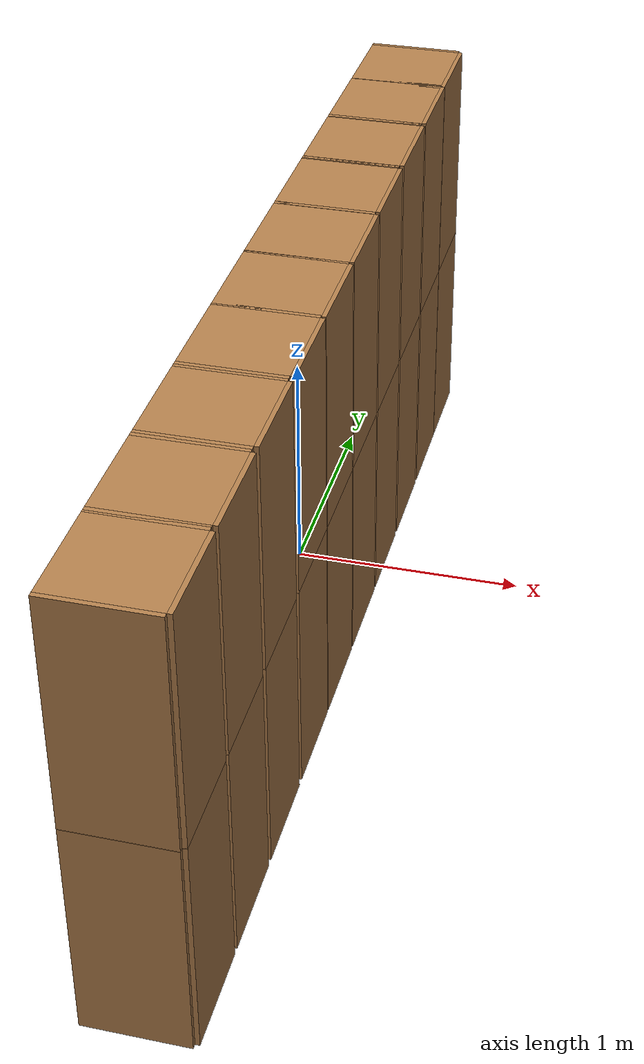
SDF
<?xml version='1.0'?>
<sdf version='1.6'>
  <model name='Locker20'>
    <model name='Locker'>
      <model name='cabinet'>
        <static>1</static>
        <link name='cabinet_bottom_plate'>
          <inertial>
            <pose frame=''>0 0 -1 0 -0 0</pose>
            <inertia>
              <ixx>2.05</ixx>
              <ixy>0</ixy>
              <ixz>0</ixz>
              <iyy>2.05</iyy>
              <iyz>0</iyz>
              <izz>2.05</izz>
            </inertia>
            <mass>25</mass>
          </inertial>
          <collision name='cabinet_bottom_plate_geom'>
            <pose frame=''>0 0 0.01 0 -0 0</pose>
            <geometry>
              <box>
                <size>0.45 0.45 0.02</size>
              </box>
            </geometry>
          </collision>
          <visual name='cabinet_bottom_plate_geom_visual'>
            <pose frame=''>0 0 0.01 0 -0 0</pose>
            <geometry>
              <box>
                <size>0.45 0.45 0.02</size>
              </box>
            </geometry>
            <material>
              <script>
                <uri>file://media/materials/scripts/gazebo.material</uri>
                <name>Gazebo/Wood</name>
              </script>
            </material>
          </visual>
          <collision name='cabinet_bottom_plate_geom_cabinet_back_plate'>
            <pose frame=''>0.235 0 0.51 0 -0 0</pose>
            <geometry>
              <box>
                <size>0.02 0.45 1.02</size>
              </box>
            </geometry>
          </collision>
          <visual name='cabinet_bottom_plate_geom_cabinet_back_plate_visual'>
            <pose frame=''>0.235 0 0.51 0 -0 0</pose>
            <geometry>
              <box>
                <size>0.02 0.45 1.02</size>
              </box>
            </geometry>
            <material>
              <script>
                <uri>file://media/materials/scripts/gazebo.material</uri>
                <name>Gazebo/Wood</name>
              </script>
            </material>
          </visual>
          <collision name='cabinet_bottom_plate_geom_cabinet_left_plate'>
            <pose frame=''>0 0.235 0.51 0 -0 0</pose>
            <geometry>
              <box>
                <size>0.45 0.02 1.02</size>
              </box>
            </geometry>
          </collision>
          <visual name='cabinet_bottom_plate_geom_cabinet_left_plate_visual'>
            <pose frame=''>0 0.235 0.51 0 -0 0</pose>
            <geometry>
              <box>
                <size>0.45 0.02 1.02</size>
              </box>
            </geometry>
            <material>
              <script>
                <uri>file://media/materials/scripts/gazebo.material</uri>
                <name>Gazebo/Wood</name>
              </script>
            </material>
          </visual>
          <collision name='cabinet_bottom_plate_geom_cabinet_middle_plate'>
            <pose frame=''>0 0 0.51 0 -0 0</pose>
            <geometry>
              <box>
                <size>0.45 0.45 0.02</size>
              </box>
            </geometry>
          </collision>
          <visual name='cabinet_bottom_plate_geom_cabinet_middle_plate_visual'>
            <pose frame=''>0 0 0.51 0 -0 0</pose>
            <geometry>
              <box>
                <size>0.45 0.45 0.02</size>
              </box>
            </geometry>
            <material>
              <script>
                <uri>file://media/materials/scripts/gazebo.material</uri>
                <name>Gazebo/Wood</name>
              </script>
            </material>
          </visual>
          <collision name='cabinet_bottom_plate_geom_cabinet_right_plate'>
            <pose frame=''>0 -0.235 0.51 0 -0 0</pose>
            <geometry>
              <box>
                <size>0.45 0.02 1.02</size>
              </box>
            </geometry>
          </collision>
          <visual name='cabinet_bottom_plate_geom_cabinet_right_plate_visual'>
            <pose frame=''>0 -0.235 0.51 0 -0 0</pose>
            <geometry>
              <box>
                <size>0.45 0.02 1.02</size>
              </box>
            </geometry>
            <material>
              <script>
                <uri>file://media/materials/scripts/gazebo.material</uri>
                <name>Gazebo/Wood</name>
              </script>
            </material>
          </visual>
          <collision name='cabinet_bottom_plate_geom_cabinet_top_plate'>
            <pose frame=''>0 0 1.01 0 -0 0</pose>
            <geometry>
              <box>
                <size>0.45 0.45 0.02</size>
              </box>
            </geometry>
          </collision>
          <visual name='cabinet_bottom_plate_geom_cabinet_top_plate_visual'>
            <pose frame=''>0 0 1.01 0 -0 0</pose>
            <geometry>
              <box>
                <size>0.45 0.45 0.02</size>
              </box>
            </geometry>
            <material>
              <script>
                <uri>file://media/materials/scripts/gazebo.material</uri>
                <name>Gazebo/Wood</name>
              </script>
            </material>
          </visual>
        </link>
        <pose frame=''>-0 2.11575 0 0 -0 0</pose>
      </model>
      <model name='cabinet_0'>
        <static>1</static>
        <link name='cabinet_bottom_plate'>
          <inertial>
            <pose frame=''>0 0 -1 0 -0 0</pose>
            <inertia>
              <ixx>2.05</ixx>
              <ixy>0</ixy>
              <ixz>0</ixz>
              <iyy>2.05</iyy>
              <iyz>0</iyz>
              <izz>2.05</izz>
            </inertia>
            <mass>25</mass>
          </inertial>
          <collision name='cabinet_bottom_plate_geom'>
            <pose frame=''>0 0 0.01 0 -0 0</pose>
            <geometry>
              <box>
                <size>0.45 0.45 0.02</size>
              </box>
            </geometry>
          </collision>
          <visual name='cabinet_bottom_plate_geom_visual'>
            <pose frame=''>0 0 0.01 0 -0 0</pose>
            <geometry>
              <box>
                <size>0.45 0.45 0.02</size>
              </box>
            </geometry>
            <material>
              <script>
                <uri>file://media/materials/scripts/gazebo.material</uri>
                <name>Gazebo/Wood</name>
              </script>
            </material>
          </visual>
          <collision name='cabinet_bottom_plate_geom_cabinet_back_plate'>
            <pose frame=''>0.235 0 0.51 0 -0 0</pose>
            <geometry>
              <box>
                <size>0.02 0.45 1.02</size>
              </box>
            </geometry>
          </collision>
          <visual name='cabinet_bottom_plate_geom_cabinet_back_plate_visual'>
            <pose frame=''>0.235 0 0.51 0 -0 0</pose>
            <geometry>
              <box>
                <size>0.02 0.45 1.02</size>
              </box>
            </geometry>
            <material>
              <script>
                <uri>file://media/materials/scripts/gazebo.material</uri>
                <name>Gazebo/Wood</name>
              </script>
            </material>
          </visual>
          <collision name='cabinet_bottom_plate_geom_cabinet_left_plate'>
            <pose frame=''>0 0.235 0.51 0 -0 0</pose>
            <geometry>
              <box>
                <size>0.45 0.02 1.02</size>
              </box>
            </geometry>
          </collision>
          <visual name='cabinet_bottom_plate_geom_cabinet_left_plate_visual'>
            <pose frame=''>0 0.235 0.51 0 -0 0</pose>
            <geometry>
              <box>
                <size>0.45 0.02 1.02</size>
              </box>
            </geometry>
            <material>
              <script>
                <uri>file://media/materials/scripts/gazebo.material</uri>
                <name>Gazebo/Wood</name>
              </script>
            </material>
          </visual>
          <collision name='cabinet_bottom_plate_geom_cabinet_middle_plate'>
            <pose frame=''>0 0 0.51 0 -0 0</pose>
            <geometry>
              <box>
                <size>0.45 0.45 0.02</size>
              </box>
            </geometry>
          </collision>
          <visual name='cabinet_bottom_plate_geom_cabinet_middle_plate_visual'>
            <pose frame=''>0 0 0.51 0 -0 0</pose>
            <geometry>
              <box>
                <size>0.45 0.45 0.02</size>
              </box>
            </geometry>
            <material>
              <script>
                <uri>file://media/materials/scripts/gazebo.material</uri>
                <name>Gazebo/Wood</name>
              </script>
            </material>
          </visual>
          <collision name='cabinet_bottom_plate_geom_cabinet_right_plate'>
            <pose frame=''>0 -0.235 0.51 0 -0 0</pose>
            <geometry>
              <box>
                <size>0.45 0.02 1.02</size>
              </box>
            </geometry>
          </collision>
          <visual name='cabinet_bottom_plate_geom_cabinet_right_plate_visual'>
            <pose frame=''>0 -0.235 0.51 0 -0 0</pose>
            <geometry>
              <box>
                <size>0.45 0.02 1.02</size>
              </box>
            </geometry>
            <material>
              <script>
                <uri>file://media/materials/scripts/gazebo.material</uri>
                <name>Gazebo/Wood</name>
              </script>
            </material>
          </visual>
          <collision name='cabinet_bottom_plate_geom_cabinet_top_plate'>
            <pose frame=''>0 0 1.01 0 -0 0</pose>
            <geometry>
              <box>
                <size>0.45 0.45 0.02</size>
              </box>
            </geometry>
          </collision>
          <visual name='cabinet_bottom_plate_geom_cabinet_top_plate_visual'>
            <pose frame=''>0 0 1.01 0 -0 0</pose>
            <geometry>
              <box>
                <size>0.45 0.45 0.02</size>
              </box>
            </geometry>
            <material>
              <script>
                <uri>file://media/materials/scripts/gazebo.material</uri>
                <name>Gazebo/Wood</name>
              </script>
            </material>
          </visual>
        </link>
        <pose frame=''>-0 1.66218 0 0 -0 0</pose>
      </model>
      <model name='cabinet_0_clone'>
        <static>1</static>
        <link name='cabinet_bottom_plate'>
          <inertial>
            <pose frame=''>0 0 -1 0 -0 0</pose>
            <inertia>
              <ixx>2.05</ixx>
              <ixy>0</ixy>
              <ixz>0</ixz>
              <iyy>2.05</iyy>
              <iyz>0</iyz>
              <izz>2.05</izz>
            </inertia>
            <mass>25</mass>
          </inertial>
          <collision name='cabinet_bottom_plate_geom'>
            <pose frame=''>0 0 0.01 0 -0 0</pose>
            <geometry>
              <box>
                <size>0.45 0.45 0.02</size>
              </box>
            </geometry>
          </collision>
          <visual name='cabinet_bottom_plate_geom_visual'>
            <pose frame=''>0 0 0.01 0 -0 0</pose>
            <geometry>
              <box>
                <size>0.45 0.45 0.02</size>
              </box>
            </geometry>
            <material>
              <script>
                <uri>file://media/materials/scripts/gazebo.material</uri>
                <name>Gazebo/Wood</name>
              </script>
            </material>
          </visual>
          <collision name='cabinet_bottom_plate_geom_cabinet_back_plate'>
            <pose frame=''>0.235 0 0.51 0 -0 0</pose>
            <geometry>
              <box>
                <size>0.02 0.45 1.02</size>
              </box>
            </geometry>
          </collision>
          <visual name='cabinet_bottom_plate_geom_cabinet_back_plate_visual'>
            <pose frame=''>0.235 0 0.51 0 -0 0</pose>
            <geometry>
              <box>
                <size>0.02 0.45 1.02</size>
              </box>
            </geometry>
            <material>
              <script>
                <uri>file://media/materials/scripts/gazebo.material</uri>
                <name>Gazebo/Wood</name>
              </script>
            </material>
          </visual>
          <collision name='cabinet_bottom_plate_geom_cabinet_left_plate'>
            <pose frame=''>0 0.235 0.51 0 -0 0</pose>
            <geometry>
              <box>
                <size>0.45 0.02 1.02</size>
              </box>
            </geometry>
          </collision>
          <visual name='cabinet_bottom_plate_geom_cabinet_left_plate_visual'>
            <pose frame=''>0 0.235 0.51 0 -0 0</pose>
            <geometry>
              <box>
                <size>0.45 0.02 1.02</size>
              </box>
            </geometry>
            <material>
              <script>
                <uri>file://media/materials/scripts/gazebo.material</uri>
                <name>Gazebo/Wood</name>
              </script>
            </material>
          </visual>
          <collision name='cabinet_bottom_plate_geom_cabinet_middle_plate'>
            <pose frame=''>0 0 0.51 0 -0 0</pose>
            <geometry>
              <box>
                <size>0.45 0.45 0.02</size>
              </box>
            </geometry>
          </collision>
          <visual name='cabinet_bottom_plate_geom_cabinet_middle_plate_visual'>
            <pose frame=''>0 0 0.51 0 -0 0</pose>
            <geometry>
              <box>
                <size>0.45 0.45 0.02</size>
              </box>
            </geometry>
            <material>
              <script>
                <uri>file://media/materials/scripts/gazebo.material</uri>
                <name>Gazebo/Wood</name>
              </script>
            </material>
          </visual>
          <collision name='cabinet_bottom_plate_geom_cabinet_right_plate'>
            <pose frame=''>0 -0.235 0.51 0 -0 0</pose>
            <geometry>
              <box>
                <size>0.45 0.02 1.02</size>
              </box>
            </geometry>
          </collision>
          <visual name='cabinet_bottom_plate_geom_cabinet_right_plate_visual'>
            <pose frame=''>0 -0.235 0.51 0 -0 0</pose>
            <geometry>
              <box>
                <size>0.45 0.02 1.02</size>
              </box>
            </geometry>
            <material>
              <script>
                <uri>file://media/materials/scripts/gazebo.material</uri>
                <name>Gazebo/Wood</name>
              </script>
            </material>
          </visual>
          <collision name='cabinet_bottom_plate_geom_cabinet_top_plate'>
            <pose frame=''>0 0 1.01 0 -0 0</pose>
            <geometry>
              <box>
                <size>0.45 0.45 0.02</size>
              </box>
            </geometry>
          </collision>
          <visual name='cabinet_bottom_plate_geom_cabinet_top_plate_visual'>
            <pose frame=''>0 0 1.01 0 -0 0</pose>
            <geometry>
              <box>
                <size>0.45 0.45 0.02</size>
              </box>
            </geometry>
            <material>
              <script>
                <uri>file://media/materials/scripts/gazebo.material</uri>
                <name>Gazebo/Wood</name>
              </script>
            </material>
          </visual>
        </link>
        <pose frame=''>-0 1.18504 0 0 -0 0</pose>
      </model>
      <model name='cabinet_0_clone_0'>
        <static>1</static>
        <link name='cabinet_bottom_plate'>
          <inertial>
            <pose frame=''>0 0 -1 0 -0 0</pose>
            <inertia>
              <ixx>2.05</ixx>
              <ixy>0</ixy>
              <ixz>0</ixz>
              <iyy>2.05</iyy>
              <iyz>0</iyz>
              <izz>2.05</izz>
            </inertia>
            <mass>25</mass>
          </inertial>
          <collision name='cabinet_bottom_plate_geom'>
            <pose frame=''>0 0 0.01 0 -0 0</pose>
            <geometry>
              <box>
                <size>0.45 0.45 0.02</size>
              </box>
            </geometry>
          </collision>
          <visual name='cabinet_bottom_plate_geom_visual'>
            <pose frame=''>0 0 0.01 0 -0 0</pose>
            <geometry>
              <box>
                <size>0.45 0.45 0.02</size>
              </box>
            </geometry>
            <material>
              <script>
                <uri>file://media/materials/scripts/gazebo.material</uri>
                <name>Gazebo/Wood</name>
              </script>
            </material>
          </visual>
          <collision name='cabinet_bottom_plate_geom_cabinet_back_plate'>
            <pose frame=''>0.235 0 0.51 0 -0 0</pose>
            <geometry>
              <box>
                <size>0.02 0.45 1.02</size>
              </box>
            </geometry>
          </collision>
          <visual name='cabinet_bottom_plate_geom_cabinet_back_plate_visual'>
            <pose frame=''>0.235 0 0.51 0 -0 0</pose>
            <geometry>
              <box>
                <size>0.02 0.45 1.02</size>
              </box>
            </geometry>
            <material>
              <script>
                <uri>file://media/materials/scripts/gazebo.material</uri>
                <name>Gazebo/Wood</name>
              </script>
            </material>
          </visual>
          <collision name='cabinet_bottom_plate_geom_cabinet_left_plate'>
            <pose frame=''>0 0.235 0.51 0 -0 0</pose>
            <geometry>
              <box>
                <size>0.45 0.02 1.02</size>
              </box>
            </geometry>
          </collision>
          <visual name='cabinet_bottom_plate_geom_cabinet_left_plate_visual'>
            <pose frame=''>0 0.235 0.51 0 -0 0</pose>
            <geometry>
              <box>
                <size>0.45 0.02 1.02</size>
              </box>
            </geometry>
            <material>
              <script>
                <uri>file://media/materials/scripts/gazebo.material</uri>
                <name>Gazebo/Wood</name>
              </script>
            </material>
          </visual>
          <collision name='cabinet_bottom_plate_geom_cabinet_middle_plate'>
            <pose frame=''>0 0 0.51 0 -0 0</pose>
            <geometry>
              <box>
                <size>0.45 0.45 0.02</size>
              </box>
            </geometry>
          </collision>
          <visual name='cabinet_bottom_plate_geom_cabinet_middle_plate_visual'>
            <pose frame=''>0 0 0.51 0 -0 0</pose>
            <geometry>
              <box>
                <size>0.45 0.45 0.02</size>
              </box>
            </geometry>
            <material>
              <script>
                <uri>file://media/materials/scripts/gazebo.material</uri>
                <name>Gazebo/Wood</name>
              </script>
            </material>
          </visual>
          <collision name='cabinet_bottom_plate_geom_cabinet_right_plate'>
            <pose frame=''>0 -0.235 0.51 0 -0 0</pose>
            <geometry>
              <box>
                <size>0.45 0.02 1.02</size>
              </box>
            </geometry>
          </collision>
          <visual name='cabinet_bottom_plate_geom_cabinet_right_plate_visual'>
            <pose frame=''>0 -0.235 0.51 0 -0 0</pose>
            <geometry>
              <box>
                <size>0.45 0.02 1.02</size>
              </box>
            </geometry>
            <material>
              <script>
                <uri>file://media/materials/scripts/gazebo.material</uri>
                <name>Gazebo/Wood</name>
              </script>
            </material>
          </visual>
          <collision name='cabinet_bottom_plate_geom_cabinet_top_plate'>
            <pose frame=''>0 0 1.01 0 -0 0</pose>
            <geometry>
              <box>
                <size>0.45 0.45 0.02</size>
              </box>
            </geometry>
          </collision>
          <visual name='cabinet_bottom_plate_geom_cabinet_top_plate_visual'>
            <pose frame=''>0 0 1.01 0 -0 0</pose>
            <geometry>
              <box>
                <size>0.45 0.45 0.02</size>
              </box>
            </geometry>
            <material>
              <script>
                <uri>file://media/materials/scripts/gazebo.material</uri>
                <name>Gazebo/Wood</name>
              </script>
            </material>
          </visual>
        </link>
        <pose frame=''>-0 0.706909 0 0 -0 0</pose>
      </model>
      <model name='cabinet_0_clone_1'>
        <static>1</static>
        <link name='cabinet_bottom_plate'>
          <inertial>
            <pose frame=''>0 0 -1 0 -0 0</pose>
            <inertia>
              <ixx>2.05</ixx>
              <ixy>0</ixy>
              <ixz>0</ixz>
              <iyy>2.05</iyy>
              <iyz>0</iyz>
              <izz>2.05</izz>
            </inertia>
            <mass>25</mass>
          </inertial>
          <collision name='cabinet_bottom_plate_geom'>
            <pose frame=''>0 0 0.01 0 -0 0</pose>
            <geometry>
              <box>
                <size>0.45 0.45 0.02</size>
              </box>
            </geometry>
          </collision>
          <visual name='cabinet_bottom_plate_geom_visual'>
            <pose frame=''>0 0 0.01 0 -0 0</pose>
            <geometry>
              <box>
                <size>0.45 0.45 0.02</size>
              </box>
            </geometry>
            <material>
              <script>
                <uri>file://media/materials/scripts/gazebo.material</uri>
                <name>Gazebo/Wood</name>
              </script>
            </material>
          </visual>
          <collision name='cabinet_bottom_plate_geom_cabinet_back_plate'>
            <pose frame=''>0.235 0 0.51 0 -0 0</pose>
            <geometry>
              <box>
                <size>0.02 0.45 1.02</size>
              </box>
            </geometry>
          </collision>
          <visual name='cabinet_bottom_plate_geom_cabinet_back_plate_visual'>
            <pose frame=''>0.235 0 0.51 0 -0 0</pose>
            <geometry>
              <box>
                <size>0.02 0.45 1.02</size>
              </box>
            </geometry>
            <material>
              <script>
                <uri>file://media/materials/scripts/gazebo.material</uri>
                <name>Gazebo/Wood</name>
              </script>
            </material>
          </visual>
          <collision name='cabinet_bottom_plate_geom_cabinet_left_plate'>
            <pose frame=''>0 0.235 0.51 0 -0 0</pose>
            <geometry>
              <box>
                <size>0.45 0.02 1.02</size>
              </box>
            </geometry>
          </collision>
          <visual name='cabinet_bottom_plate_geom_cabinet_left_plate_visual'>
            <pose frame=''>0 0.235 0.51 0 -0 0</pose>
            <geometry>
              <box>
                <size>0.45 0.02 1.02</size>
              </box>
            </geometry>
            <material>
              <script>
                <uri>file://media/materials/scripts/gazebo.material</uri>
                <name>Gazebo/Wood</name>
              </script>
            </material>
          </visual>
          <collision name='cabinet_bottom_plate_geom_cabinet_middle_plate'>
            <pose frame=''>0 0 0.51 0 -0 0</pose>
            <geometry>
              <box>
                <size>0.45 0.45 0.02</size>
              </box>
            </geometry>
          </collision>
          <visual name='cabinet_bottom_plate_geom_cabinet_middle_plate_visual'>
            <pose frame=''>0 0 0.51 0 -0 0</pose>
            <geometry>
              <box>
                <size>0.45 0.45 0.02</size>
              </box>
            </geometry>
            <material>
              <script>
                <uri>file://media/materials/scripts/gazebo.material</uri>
                <name>Gazebo/Wood</name>
              </script>
            </material>
          </visual>
          <collision name='cabinet_bottom_plate_geom_cabinet_right_plate'>
            <pose frame=''>0 -0.235 0.51 0 -0 0</pose>
            <geometry>
              <box>
                <size>0.45 0.02 1.02</size>
              </box>
            </geometry>
          </collision>
          <visual name='cabinet_bottom_plate_geom_cabinet_right_plate_visual'>
            <pose frame=''>0 -0.235 0.51 0 -0 0</pose>
            <geometry>
              <box>
                <size>0.45 0.02 1.02</size>
              </box>
            </geometry>
            <material>
              <script>
                <uri>file://media/materials/scripts/gazebo.material</uri>
                <name>Gazebo/Wood</name>
              </script>
            </material>
          </visual>
          <collision name='cabinet_bottom_plate_geom_cabinet_top_plate'>
            <pose frame=''>0 0 1.01 0 -0 0</pose>
            <geometry>
              <box>
                <size>0.45 0.45 0.02</size>
              </box>
            </geometry>
          </collision>
          <visual name='cabinet_bottom_plate_geom_cabinet_top_plate_visual'>
            <pose frame=''>0 0 1.01 0 -0 0</pose>
            <geometry>
              <box>
                <size>0.45 0.45 0.02</size>
              </box>
            </geometry>
            <material>
              <script>
                <uri>file://media/materials/scripts/gazebo.material</uri>
                <name>Gazebo/Wood</name>
              </script>
            </material>
          </visual>
        </link>
        <pose frame=''>-0 0.23468 0 0 -0 0</pose>
      </model>
      <model name='cabinet_0_clone_2'>
        <static>1</static>
        <link name='cabinet_bottom_plate'>
          <inertial>
            <pose frame=''>0 0 -1 0 -0 0</pose>
            <inertia>
              <ixx>2.05</ixx>
              <ixy>0</ixy>
              <ixz>0</ixz>
              <iyy>2.05</iyy>
              <iyz>0</iyz>
              <izz>2.05</izz>
            </inertia>
            <mass>25</mass>
          </inertial>
          <collision name='cabinet_bottom_plate_geom'>
            <pose frame=''>0 0 0.01 0 -0 0</pose>
            <geometry>
              <box>
                <size>0.45 0.45 0.02</size>
              </box>
            </geometry>
          </collision>
          <visual name='cabinet_bottom_plate_geom_visual'>
            <pose frame=''>0 0 0.01 0 -0 0</pose>
            <geometry>
              <box>
                <size>0.45 0.45 0.02</size>
              </box>
            </geometry>
            <material>
              <script>
                <uri>file://media/materials/scripts/gazebo.material</uri>
                <name>Gazebo/Wood</name>
              </script>
            </material>
          </visual>
          <collision name='cabinet_bottom_plate_geom_cabinet_back_plate'>
            <pose frame=''>0.235 0 0.51 0 -0 0</pose>
            <geometry>
              <box>
                <size>0.02 0.45 1.02</size>
              </box>
            </geometry>
          </collision>
          <visual name='cabinet_bottom_plate_geom_cabinet_back_plate_visual'>
            <pose frame=''>0.235 0 0.51 0 -0 0</pose>
            <geometry>
              <box>
                <size>0.02 0.45 1.02</size>
              </box>
            </geometry>
            <material>
              <script>
                <uri>file://media/materials/scripts/gazebo.material</uri>
                <name>Gazebo/Wood</name>
              </script>
            </material>
          </visual>
          <collision name='cabinet_bottom_plate_geom_cabinet_left_plate'>
            <pose frame=''>0 0.235 0.51 0 -0 0</pose>
            <geometry>
              <box>
                <size>0.45 0.02 1.02</size>
              </box>
            </geometry>
          </collision>
          <visual name='cabinet_bottom_plate_geom_cabinet_left_plate_visual'>
            <pose frame=''>0 0.235 0.51 0 -0 0</pose>
            <geometry>
              <box>
                <size>0.45 0.02 1.02</size>
              </box>
            </geometry>
            <material>
              <script>
                <uri>file://media/materials/scripts/gazebo.material</uri>
                <name>Gazebo/Wood</name>
              </script>
            </material>
          </visual>
          <collision name='cabinet_bottom_plate_geom_cabinet_middle_plate'>
            <pose frame=''>0 0 0.51 0 -0 0</pose>
            <geometry>
              <box>
                <size>0.45 0.45 0.02</size>
              </box>
            </geometry>
          </collision>
          <visual name='cabinet_bottom_plate_geom_cabinet_middle_plate_visual'>
            <pose frame=''>0 0 0.51 0 -0 0</pose>
            <geometry>
              <box>
                <size>0.45 0.45 0.02</size>
              </box>
            </geometry>
            <material>
              <script>
                <uri>file://media/materials/scripts/gazebo.material</uri>
                <name>Gazebo/Wood</name>
              </script>
            </material>
          </visual>
          <collision name='cabinet_bottom_plate_geom_cabinet_right_plate'>
            <pose frame=''>0 -0.235 0.51 0 -0 0</pose>
            <geometry>
              <box>
                <size>0.45 0.02 1.02</size>
              </box>
            </geometry>
          </collision>
          <visual name='cabinet_bottom_plate_geom_cabinet_right_plate_visual'>
            <pose frame=''>0 -0.235 0.51 0 -0 0</pose>
            <geometry>
              <box>
                <size>0.45 0.02 1.02</size>
              </box>
            </geometry>
            <material>
              <script>
                <uri>file://media/materials/scripts/gazebo.material</uri>
                <name>Gazebo/Wood</name>
              </script>
            </material>
          </visual>
          <collision name='cabinet_bottom_plate_geom_cabinet_top_plate'>
            <pose frame=''>0 0 1.01 0 -0 0</pose>
            <geometry>
              <box>
                <size>0.45 0.45 0.02</size>
              </box>
            </geometry>
          </collision>
          <visual name='cabinet_bottom_plate_geom_cabinet_top_plate_visual'>
            <pose frame=''>0 0 1.01 0 -0 0</pose>
            <geometry>
              <box>
                <size>0.45 0.45 0.02</size>
              </box>
            </geometry>
            <material>
              <script>
                <uri>file://media/materials/scripts/gazebo.material</uri>
                <name>Gazebo/Wood</name>
              </script>
            </material>
          </visual>
        </link>
        <pose frame=''>-0 -0.229028 0 0 -0 0</pose>
      </model>
      <model name='cabinet_0_clone_3'>
        <static>1</static>
        <link name='cabinet_bottom_plate'>
          <inertial>
            <pose frame=''>0 0 -1 0 -0 0</pose>
            <inertia>
              <ixx>2.05</ixx>
              <ixy>0</ixy>
              <ixz>0</ixz>
              <iyy>2.05</iyy>
              <iyz>0</iyz>
              <izz>2.05</izz>
            </inertia>
            <mass>25</mass>
          </inertial>
          <collision name='cabinet_bottom_plate_geom'>
            <pose frame=''>0 0 0.01 0 -0 0</pose>
            <geometry>
              <box>
                <size>0.45 0.45 0.02</size>
              </box>
            </geometry>
          </collision>
          <visual name='cabinet_bottom_plate_geom_visual'>
            <pose frame=''>0 0 0.01 0 -0 0</pose>
            <geometry>
              <box>
                <size>0.45 0.45 0.02</size>
              </box>
            </geometry>
            <material>
              <script>
                <uri>file://media/materials/scripts/gazebo.material</uri>
                <name>Gazebo/Wood</name>
              </script>
            </material>
          </visual>
          <collision name='cabinet_bottom_plate_geom_cabinet_back_plate'>
            <pose frame=''>0.235 0 0.51 0 -0 0</pose>
            <geometry>
              <box>
                <size>0.02 0.45 1.02</size>
              </box>
            </geometry>
          </collision>
          <visual name='cabinet_bottom_plate_geom_cabinet_back_plate_visual'>
            <pose frame=''>0.235 0 0.51 0 -0 0</pose>
            <geometry>
              <box>
                <size>0.02 0.45 1.02</size>
              </box>
            </geometry>
            <material>
              <script>
                <uri>file://media/materials/scripts/gazebo.material</uri>
                <name>Gazebo/Wood</name>
              </script>
            </material>
          </visual>
          <collision name='cabinet_bottom_plate_geom_cabinet_left_plate'>
            <pose frame=''>0 0.235 0.51 0 -0 0</pose>
            <geometry>
              <box>
                <size>0.45 0.02 1.02</size>
              </box>
            </geometry>
          </collision>
          <visual name='cabinet_bottom_plate_geom_cabinet_left_plate_visual'>
            <pose frame=''>0 0.235 0.51 0 -0 0</pose>
            <geometry>
              <box>
                <size>0.45 0.02 1.02</size>
              </box>
            </geometry>
            <material>
              <script>
                <uri>file://media/materials/scripts/gazebo.material</uri>
                <name>Gazebo/Wood</name>
              </script>
            </material>
          </visual>
          <collision name='cabinet_bottom_plate_geom_cabinet_middle_plate'>
            <pose frame=''>0 0 0.51 0 -0 0</pose>
            <geometry>
              <box>
                <size>0.45 0.45 0.02</size>
              </box>
            </geometry>
          </collision>
          <visual name='cabinet_bottom_plate_geom_cabinet_middle_plate_visual'>
            <pose frame=''>0 0 0.51 0 -0 0</pose>
            <geometry>
              <box>
                <size>0.45 0.45 0.02</size>
              </box>
            </geometry>
            <material>
              <script>
                <uri>file://media/materials/scripts/gazebo.material</uri>
                <name>Gazebo/Wood</name>
              </script>
            </material>
          </visual>
          <collision name='cabinet_bottom_plate_geom_cabinet_right_plate'>
            <pose frame=''>0 -0.235 0.51 0 -0 0</pose>
            <geometry>
              <box>
                <size>0.45 0.02 1.02</size>
              </box>
            </geometry>
          </collision>
          <visual name='cabinet_bottom_plate_geom_cabinet_right_plate_visual'>
            <pose frame=''>0 -0.235 0.51 0 -0 0</pose>
            <geometry>
              <box>
                <size>0.45 0.02 1.02</size>
              </box>
            </geometry>
            <material>
              <script>
                <uri>file://media/materials/scripts/gazebo.material</uri>
                <name>Gazebo/Wood</name>
              </script>
            </material>
          </visual>
          <collision name='cabinet_bottom_plate_geom_cabinet_top_plate'>
            <pose frame=''>0 0 1.01 0 -0 0</pose>
            <geometry>
              <box>
                <size>0.45 0.45 0.02</size>
              </box>
            </geometry>
          </collision>
          <visual name='cabinet_bottom_plate_geom_cabinet_top_plate_visual'>
            <pose frame=''>0 0 1.01 0 -0 0</pose>
            <geometry>
              <box>
                <size>0.45 0.45 0.02</size>
              </box>
            </geometry>
            <material>
              <script>
                <uri>file://media/materials/scripts/gazebo.material</uri>
                <name>Gazebo/Wood</name>
              </script>
            </material>
          </visual>
        </link>
        <pose frame=''>-0 -0.689433 0 0 -0 0</pose>
      </model>
      <model name='cabinet_0_clone_4'>
        <static>1</static>
        <link name='cabinet_bottom_plate'>
          <inertial>
            <pose frame=''>0 0 -1 0 -0 0</pose>
            <inertia>
              <ixx>2.05</ixx>
              <ixy>0</ixy>
              <ixz>0</ixz>
              <iyy>2.05</iyy>
              <iyz>0</iyz>
              <izz>2.05</izz>
            </inertia>
            <mass>25</mass>
          </inertial>
          <collision name='cabinet_bottom_plate_geom'>
            <pose frame=''>0 0 0.01 0 -0 0</pose>
            <geometry>
              <box>
                <size>0.45 0.45 0.02</size>
              </box>
            </geometry>
          </collision>
          <visual name='cabinet_bottom_plate_geom_visual'>
            <pose frame=''>0 0 0.01 0 -0 0</pose>
            <geometry>
              <box>
                <size>0.45 0.45 0.02</size>
              </box>
            </geometry>
            <material>
              <script>
                <uri>file://media/materials/scripts/gazebo.material</uri>
                <name>Gazebo/Wood</name>
              </script>
            </material>
          </visual>
          <collision name='cabinet_bottom_plate_geom_cabinet_back_plate'>
            <pose frame=''>0.235 0 0.51 0 -0 0</pose>
            <geometry>
              <box>
                <size>0.02 0.45 1.02</size>
              </box>
            </geometry>
          </collision>
          <visual name='cabinet_bottom_plate_geom_cabinet_back_plate_visual'>
            <pose frame=''>0.235 0 0.51 0 -0 0</pose>
            <geometry>
              <box>
                <size>0.02 0.45 1.02</size>
              </box>
            </geometry>
            <material>
              <script>
                <uri>file://media/materials/scripts/gazebo.material</uri>
                <name>Gazebo/Wood</name>
              </script>
            </material>
          </visual>
          <collision name='cabinet_bottom_plate_geom_cabinet_left_plate'>
            <pose frame=''>0 0.235 0.51 0 -0 0</pose>
            <geometry>
              <box>
                <size>0.45 0.02 1.02</size>
              </box>
            </geometry>
          </collision>
          <visual name='cabinet_bottom_plate_geom_cabinet_left_plate_visual'>
            <pose frame=''>0 0.235 0.51 0 -0 0</pose>
            <geometry>
              <box>
                <size>0.45 0.02 1.02</size>
              </box>
            </geometry>
            <material>
              <script>
                <uri>file://media/materials/scripts/gazebo.material</uri>
                <name>Gazebo/Wood</name>
              </script>
            </material>
          </visual>
          <collision name='cabinet_bottom_plate_geom_cabinet_middle_plate'>
            <pose frame=''>0 0 0.51 0 -0 0</pose>
            <geometry>
              <box>
                <size>0.45 0.45 0.02</size>
              </box>
            </geometry>
          </collision>
          <visual name='cabinet_bottom_plate_geom_cabinet_middle_plate_visual'>
            <pose frame=''>0 0 0.51 0 -0 0</pose>
            <geometry>
              <box>
                <size>0.45 0.45 0.02</size>
              </box>
            </geometry>
            <material>
              <script>
                <uri>file://media/materials/scripts/gazebo.material</uri>
                <name>Gazebo/Wood</name>
              </script>
            </material>
          </visual>
          <collision name='cabinet_bottom_plate_geom_cabinet_right_plate'>
            <pose frame=''>0 -0.235 0.51 0 -0 0</pose>
            <geometry>
              <box>
                <size>0.45 0.02 1.02</size>
              </box>
            </geometry>
          </collision>
          <visual name='cabinet_bottom_plate_geom_cabinet_right_plate_visual'>
            <pose frame=''>0 -0.235 0.51 0 -0 0</pose>
            <geometry>
              <box>
                <size>0.45 0.02 1.02</size>
              </box>
            </geometry>
            <material>
              <script>
                <uri>file://media/materials/scripts/gazebo.material</uri>
                <name>Gazebo/Wood</name>
              </script>
            </material>
          </visual>
          <collision name='cabinet_bottom_plate_geom_cabinet_top_plate'>
            <pose frame=''>0 0 1.01 0 -0 0</pose>
            <geometry>
              <box>
                <size>0.45 0.45 0.02</size>
              </box>
            </geometry>
          </collision>
          <visual name='cabinet_bottom_plate_geom_cabinet_top_plate_visual'>
            <pose frame=''>0 0 1.01 0 -0 0</pose>
            <geometry>
              <box>
                <size>0.45 0.45 0.02</size>
              </box>
            </geometry>
            <material>
              <script>
                <uri>file://media/materials/scripts/gazebo.material</uri>
                <name>Gazebo/Wood</name>
              </script>
            </material>
          </visual>
        </link>
        <pose frame=''>-0 -1.17658 0 0 -0 0</pose>
      </model>
      <model name='cabinet_0_clone_5'>
        <static>1</static>
        <link name='cabinet_bottom_plate'>
          <inertial>
            <pose frame=''>0 0 -1 0 -0 0</pose>
            <inertia>
              <ixx>2.05</ixx>
              <ixy>0</ixy>
              <ixz>0</ixz>
              <iyy>2.05</iyy>
              <iyz>0</iyz>
              <izz>2.05</izz>
            </inertia>
            <mass>25</mass>
          </inertial>
          <collision name='cabinet_bottom_plate_geom'>
            <pose frame=''>0 0 0.01 0 -0 0</pose>
            <geometry>
              <box>
                <size>0.45 0.45 0.02</size>
              </box>
            </geometry>
          </collision>
          <visual name='cabinet_bottom_plate_geom_visual'>
            <pose frame=''>0 0 0.01 0 -0 0</pose>
            <geometry>
              <box>
                <size>0.45 0.45 0.02</size>
              </box>
            </geometry>
            <material>
              <script>
                <uri>file://media/materials/scripts/gazebo.material</uri>
                <name>Gazebo/Wood</name>
              </script>
            </material>
          </visual>
          <collision name='cabinet_bottom_plate_geom_cabinet_back_plate'>
            <pose frame=''>0.235 0 0.51 0 -0 0</pose>
            <geometry>
              <box>
                <size>0.02 0.45 1.02</size>
              </box>
            </geometry>
          </collision>
          <visual name='cabinet_bottom_plate_geom_cabinet_back_plate_visual'>
            <pose frame=''>0.235 0 0.51 0 -0 0</pose>
            <geometry>
              <box>
                <size>0.02 0.45 1.02</size>
              </box>
            </geometry>
            <material>
              <script>
                <uri>file://media/materials/scripts/gazebo.material</uri>
                <name>Gazebo/Wood</name>
              </script>
            </material>
          </visual>
          <collision name='cabinet_bottom_plate_geom_cabinet_left_plate'>
            <pose frame=''>0 0.235 0.51 0 -0 0</pose>
            <geometry>
              <box>
                <size>0.45 0.02 1.02</size>
              </box>
            </geometry>
          </collision>
          <visual name='cabinet_bottom_plate_geom_cabinet_left_plate_visual'>
            <pose frame=''>0 0.235 0.51 0 -0 0</pose>
            <geometry>
              <box>
                <size>0.45 0.02 1.02</size>
              </box>
            </geometry>
            <material>
              <script>
                <uri>file://media/materials/scripts/gazebo.material</uri>
                <name>Gazebo/Wood</name>
              </script>
            </material>
          </visual>
          <collision name='cabinet_bottom_plate_geom_cabinet_middle_plate'>
            <pose frame=''>0 0 0.51 0 -0 0</pose>
            <geometry>
              <box>
                <size>0.45 0.45 0.02</size>
              </box>
            </geometry>
          </collision>
          <visual name='cabinet_bottom_plate_geom_cabinet_middle_plate_visual'>
            <pose frame=''>0 0 0.51 0 -0 0</pose>
            <geometry>
              <box>
                <size>0.45 0.45 0.02</size>
              </box>
            </geometry>
            <material>
              <script>
                <uri>file://media/materials/scripts/gazebo.material</uri>
                <name>Gazebo/Wood</name>
              </script>
            </material>
          </visual>
          <collision name='cabinet_bottom_plate_geom_cabinet_right_plate'>
            <pose frame=''>0 -0.235 0.51 0 -0 0</pose>
            <geometry>
              <box>
                <size>0.45 0.02 1.02</size>
              </box>
            </geometry>
          </collision>
          <visual name='cabinet_bottom_plate_geom_cabinet_right_plate_visual'>
            <pose frame=''>0 -0.235 0.51 0 -0 0</pose>
            <geometry>
              <box>
                <size>0.45 0.02 1.02</size>
              </box>
            </geometry>
            <material>
              <script>
                <uri>file://media/materials/scripts/gazebo.material</uri>
                <name>Gazebo/Wood</name>
              </script>
            </material>
          </visual>
          <collision name='cabinet_bottom_plate_geom_cabinet_top_plate'>
            <pose frame=''>0 0 1.01 0 -0 0</pose>
            <geometry>
              <box>
                <size>0.45 0.45 0.02</size>
              </box>
            </geometry>
          </collision>
          <visual name='cabinet_bottom_plate_geom_cabinet_top_plate_visual'>
            <pose frame=''>0 0 1.01 0 -0 0</pose>
            <geometry>
              <box>
                <size>0.45 0.45 0.02</size>
              </box>
            </geometry>
            <material>
              <script>
                <uri>file://media/materials/scripts/gazebo.material</uri>
                <name>Gazebo/Wood</name>
              </script>
            </material>
          </visual>
        </link>
        <pose frame=''>-0 -1.6643 0 0 -0 0</pose>
      </model>
      <model name='cabinet_0_clone_6'>
        <static>1</static>
        <link name='cabinet_bottom_plate'>
          <inertial>
            <pose frame=''>0 0 -1 0 -0 0</pose>
            <inertia>
              <ixx>2.05</ixx>
              <ixy>0</ixy>
              <ixz>0</ixz>
              <iyy>2.05</iyy>
              <iyz>0</iyz>
              <izz>2.05</izz>
            </inertia>
            <mass>25</mass>
          </inertial>
          <collision name='cabinet_bottom_plate_geom'>
            <pose frame=''>0 0 0.01 0 -0 0</pose>
            <geometry>
              <box>
                <size>0.45 0.45 0.02</size>
              </box>
            </geometry>
          </collision>
          <visual name='cabinet_bottom_plate_geom_visual'>
            <pose frame=''>0 0 0.01 0 -0 0</pose>
            <geometry>
              <box>
                <size>0.45 0.45 0.02</size>
              </box>
            </geometry>
            <material>
              <script>
                <uri>file://media/materials/scripts/gazebo.material</uri>
                <name>Gazebo/Wood</name>
              </script>
            </material>
          </visual>
          <collision name='cabinet_bottom_plate_geom_cabinet_back_plate'>
            <pose frame=''>0.235 0 0.51 0 -0 0</pose>
            <geometry>
              <box>
                <size>0.02 0.45 1.02</size>
              </box>
            </geometry>
          </collision>
          <visual name='cabinet_bottom_plate_geom_cabinet_back_plate_visual'>
            <pose frame=''>0.235 0 0.51 0 -0 0</pose>
            <geometry>
              <box>
                <size>0.02 0.45 1.02</size>
              </box>
            </geometry>
            <material>
              <script>
                <uri>file://media/materials/scripts/gazebo.material</uri>
                <name>Gazebo/Wood</name>
              </script>
            </material>
          </visual>
          <collision name='cabinet_bottom_plate_geom_cabinet_left_plate'>
            <pose frame=''>0 0.235 0.51 0 -0 0</pose>
            <geometry>
              <box>
                <size>0.45 0.02 1.02</size>
              </box>
            </geometry>
          </collision>
          <visual name='cabinet_bottom_plate_geom_cabinet_left_plate_visual'>
            <pose frame=''>0 0.235 0.51 0 -0 0</pose>
            <geometry>
              <box>
                <size>0.45 0.02 1.02</size>
              </box>
            </geometry>
            <material>
              <script>
                <uri>file://media/materials/scripts/gazebo.material</uri>
                <name>Gazebo/Wood</name>
              </script>
            </material>
          </visual>
          <collision name='cabinet_bottom_plate_geom_cabinet_middle_plate'>
            <pose frame=''>0 0 0.51 0 -0 0</pose>
            <geometry>
              <box>
                <size>0.45 0.45 0.02</size>
              </box>
            </geometry>
          </collision>
          <visual name='cabinet_bottom_plate_geom_cabinet_middle_plate_visual'>
            <pose frame=''>0 0 0.51 0 -0 0</pose>
            <geometry>
              <box>
                <size>0.45 0.45 0.02</size>
              </box>
            </geometry>
            <material>
              <script>
                <uri>file://media/materials/scripts/gazebo.material</uri>
                <name>Gazebo/Wood</name>
              </script>
            </material>
          </visual>
          <collision name='cabinet_bottom_plate_geom_cabinet_right_plate'>
            <pose frame=''>0 -0.235 0.51 0 -0 0</pose>
            <geometry>
              <box>
                <size>0.45 0.02 1.02</size>
              </box>
            </geometry>
          </collision>
          <visual name='cabinet_bottom_plate_geom_cabinet_right_plate_visual'>
            <pose frame=''>0 -0.235 0.51 0 -0 0</pose>
            <geometry>
              <box>
                <size>0.45 0.02 1.02</size>
              </box>
            </geometry>
            <material>
              <script>
                <uri>file://media/materials/scripts/gazebo.material</uri>
                <name>Gazebo/Wood</name>
              </script>
            </material>
          </visual>
          <collision name='cabinet_bottom_plate_geom_cabinet_top_plate'>
            <pose frame=''>0 0 1.01 0 -0 0</pose>
            <geometry>
              <box>
                <size>0.45 0.45 0.02</size>
              </box>
            </geometry>
          </collision>
          <visual name='cabinet_bottom_plate_geom_cabinet_top_plate_visual'>
            <pose frame=''>0 0 1.01 0 -0 0</pose>
            <geometry>
              <box>
                <size>0.45 0.45 0.02</size>
              </box>
            </geometry>
            <material>
              <script>
                <uri>file://media/materials/scripts/gazebo.material</uri>
                <name>Gazebo/Wood</name>
              </script>
            </material>
          </visual>
        </link>
        <pose frame=''>-0 -2.14521 0 0 -0 0</pose>
      </model>
      <static>0</static>
      <allow_auto_disable>1</allow_auto_disable>
      <pose frame=''>0 -0 0.511061 0 -0 0</pose>
    </model>
    <model name='Locker_0'>
      <model name='cabinet'>
        <static>1</static>
        <link name='cabinet_bottom_plate'>
          <inertial>
            <pose frame=''>0 0 -1 0 -0 0</pose>
            <inertia>
              <ixx>2.05</ixx>
              <ixy>0</ixy>
              <ixz>0</ixz>
              <iyy>2.05</iyy>
              <iyz>0</iyz>
              <izz>2.05</izz>
            </inertia>
            <mass>25</mass>
          </inertial>
          <collision name='cabinet_bottom_plate_geom'>
            <pose frame=''>0 0 0.01 0 -0 0</pose>
            <geometry>
              <box>
                <size>0.45 0.45 0.02</size>
              </box>
            </geometry>
          </collision>
          <visual name='cabinet_bottom_plate_geom_visual'>
            <pose frame=''>0 0 0.01 0 -0 0</pose>
            <geometry>
              <box>
                <size>0.45 0.45 0.02</size>
              </box>
            </geometry>
            <material>
              <script>
                <uri>file://media/materials/scripts/gazebo.material</uri>
                <name>Gazebo/Wood</name>
              </script>
            </material>
          </visual>
          <collision name='cabinet_bottom_plate_geom_cabinet_back_plate'>
            <pose frame=''>0.235 0 0.51 0 -0 0</pose>
            <geometry>
              <box>
                <size>0.02 0.45 1.02</size>
              </box>
            </geometry>
          </collision>
          <visual name='cabinet_bottom_plate_geom_cabinet_back_plate_visual'>
            <pose frame=''>0.235 0 0.51 0 -0 0</pose>
            <geometry>
              <box>
                <size>0.02 0.45 1.02</size>
              </box>
            </geometry>
            <material>
              <script>
                <uri>file://media/materials/scripts/gazebo.material</uri>
                <name>Gazebo/Wood</name>
              </script>
            </material>
          </visual>
          <collision name='cabinet_bottom_plate_geom_cabinet_left_plate'>
            <pose frame=''>0 0.235 0.51 0 -0 0</pose>
            <geometry>
              <box>
                <size>0.45 0.02 1.02</size>
              </box>
            </geometry>
          </collision>
          <visual name='cabinet_bottom_plate_geom_cabinet_left_plate_visual'>
            <pose frame=''>0 0.235 0.51 0 -0 0</pose>
            <geometry>
              <box>
                <size>0.45 0.02 1.02</size>
              </box>
            </geometry>
            <material>
              <script>
                <uri>file://media/materials/scripts/gazebo.material</uri>
                <name>Gazebo/Wood</name>
              </script>
            </material>
          </visual>
          <collision name='cabinet_bottom_plate_geom_cabinet_middle_plate'>
            <pose frame=''>0 0 0.51 0 -0 0</pose>
            <geometry>
              <box>
                <size>0.45 0.45 0.02</size>
              </box>
            </geometry>
          </collision>
          <visual name='cabinet_bottom_plate_geom_cabinet_middle_plate_visual'>
            <pose frame=''>0 0 0.51 0 -0 0</pose>
            <geometry>
              <box>
                <size>0.45 0.45 0.02</size>
              </box>
            </geometry>
            <material>
              <script>
                <uri>file://media/materials/scripts/gazebo.material</uri>
                <name>Gazebo/Wood</name>
              </script>
            </material>
          </visual>
          <collision name='cabinet_bottom_plate_geom_cabinet_right_plate'>
            <pose frame=''>0 -0.235 0.51 0 -0 0</pose>
            <geometry>
              <box>
                <size>0.45 0.02 1.02</size>
              </box>
            </geometry>
          </collision>
          <visual name='cabinet_bottom_plate_geom_cabinet_right_plate_visual'>
            <pose frame=''>0 -0.235 0.51 0 -0 0</pose>
            <geometry>
              <box>
                <size>0.45 0.02 1.02</size>
              </box>
            </geometry>
            <material>
              <script>
                <uri>file://media/materials/scripts/gazebo.material</uri>
                <name>Gazebo/Wood</name>
              </script>
            </material>
          </visual>
          <collision name='cabinet_bottom_plate_geom_cabinet_top_plate'>
            <pose frame=''>0 0 1.01 0 -0 0</pose>
            <geometry>
              <box>
                <size>0.45 0.45 0.02</size>
              </box>
            </geometry>
          </collision>
          <visual name='cabinet_bottom_plate_geom_cabinet_top_plate_visual'>
            <pose frame=''>0 0 1.01 0 -0 0</pose>
            <geometry>
              <box>
                <size>0.45 0.45 0.02</size>
              </box>
            </geometry>
            <material>
              <script>
                <uri>file://media/materials/scripts/gazebo.material</uri>
                <name>Gazebo/Wood</name>
              </script>
            </material>
          </visual>
        </link>
        <pose frame=''>-0 2.11575 0 0 -0 0</pose>
      </model>
      <model name='cabinet_0'>
        <static>1</static>
        <link name='cabinet_bottom_plate'>
          <inertial>
            <pose frame=''>0 0 -1 0 -0 0</pose>
            <inertia>
              <ixx>2.05</ixx>
              <ixy>0</ixy>
              <ixz>0</ixz>
              <iyy>2.05</iyy>
              <iyz>0</iyz>
              <izz>2.05</izz>
            </inertia>
            <mass>25</mass>
          </inertial>
          <collision name='cabinet_bottom_plate_geom'>
            <pose frame=''>0 0 0.01 0 -0 0</pose>
            <geometry>
              <box>
                <size>0.45 0.45 0.02</size>
              </box>
            </geometry>
          </collision>
          <visual name='cabinet_bottom_plate_geom_visual'>
            <pose frame=''>0 0 0.01 0 -0 0</pose>
            <geometry>
              <box>
                <size>0.45 0.45 0.02</size>
              </box>
            </geometry>
            <material>
              <script>
                <uri>file://media/materials/scripts/gazebo.material</uri>
                <name>Gazebo/Wood</name>
              </script>
            </material>
          </visual>
          <collision name='cabinet_bottom_plate_geom_cabinet_back_plate'>
            <pose frame=''>0.235 0 0.51 0 -0 0</pose>
            <geometry>
              <box>
                <size>0.02 0.45 1.02</size>
              </box>
            </geometry>
          </collision>
          <visual name='cabinet_bottom_plate_geom_cabinet_back_plate_visual'>
            <pose frame=''>0.235 0 0.51 0 -0 0</pose>
            <geometry>
              <box>
                <size>0.02 0.45 1.02</size>
              </box>
            </geometry>
            <material>
              <script>
                <uri>file://media/materials/scripts/gazebo.material</uri>
                <name>Gazebo/Wood</name>
              </script>
            </material>
          </visual>
          <collision name='cabinet_bottom_plate_geom_cabinet_left_plate'>
            <pose frame=''>0 0.235 0.51 0 -0 0</pose>
            <geometry>
              <box>
                <size>0.45 0.02 1.02</size>
              </box>
            </geometry>
          </collision>
          <visual name='cabinet_bottom_plate_geom_cabinet_left_plate_visual'>
            <pose frame=''>0 0.235 0.51 0 -0 0</pose>
            <geometry>
              <box>
                <size>0.45 0.02 1.02</size>
              </box>
            </geometry>
            <material>
              <script>
                <uri>file://media/materials/scripts/gazebo.material</uri>
                <name>Gazebo/Wood</name>
              </script>
            </material>
          </visual>
          <collision name='cabinet_bottom_plate_geom_cabinet_middle_plate'>
            <pose frame=''>0 0 0.51 0 -0 0</pose>
            <geometry>
              <box>
                <size>0.45 0.45 0.02</size>
              </box>
            </geometry>
          </collision>
          <visual name='cabinet_bottom_plate_geom_cabinet_middle_plate_visual'>
            <pose frame=''>0 0 0.51 0 -0 0</pose>
            <geometry>
              <box>
                <size>0.45 0.45 0.02</size>
              </box>
            </geometry>
            <material>
              <script>
                <uri>file://media/materials/scripts/gazebo.material</uri>
                <name>Gazebo/Wood</name>
              </script>
            </material>
          </visual>
          <collision name='cabinet_bottom_plate_geom_cabinet_right_plate'>
            <pose frame=''>0 -0.235 0.51 0 -0 0</pose>
            <geometry>
              <box>
                <size>0.45 0.02 1.02</size>
              </box>
            </geometry>
          </collision>
          <visual name='cabinet_bottom_plate_geom_cabinet_right_plate_visual'>
            <pose frame=''>0 -0.235 0.51 0 -0 0</pose>
            <geometry>
              <box>
                <size>0.45 0.02 1.02</size>
              </box>
            </geometry>
            <material>
              <script>
                <uri>file://media/materials/scripts/gazebo.material</uri>
                <name>Gazebo/Wood</name>
              </script>
            </material>
          </visual>
          <collision name='cabinet_bottom_plate_geom_cabinet_top_plate'>
            <pose frame=''>0 0 1.01 0 -0 0</pose>
            <geometry>
              <box>
                <size>0.45 0.45 0.02</size>
              </box>
            </geometry>
          </collision>
          <visual name='cabinet_bottom_plate_geom_cabinet_top_plate_visual'>
            <pose frame=''>0 0 1.01 0 -0 0</pose>
            <geometry>
              <box>
                <size>0.45 0.45 0.02</size>
              </box>
            </geometry>
            <material>
              <script>
                <uri>file://media/materials/scripts/gazebo.material</uri>
                <name>Gazebo/Wood</name>
              </script>
            </material>
          </visual>
        </link>
        <pose frame=''>-0 1.66218 0 0 -0 0</pose>
      </model>
      <model name='cabinet_0_clone'>
        <static>1</static>
        <link name='cabinet_bottom_plate'>
          <inertial>
            <pose frame=''>0 0 -1 0 -0 0</pose>
            <inertia>
              <ixx>2.05</ixx>
              <ixy>0</ixy>
              <ixz>0</ixz>
              <iyy>2.05</iyy>
              <iyz>0</iyz>
              <izz>2.05</izz>
            </inertia>
            <mass>25</mass>
          </inertial>
          <collision name='cabinet_bottom_plate_geom'>
            <pose frame=''>0 0 0.01 0 -0 0</pose>
            <geometry>
              <box>
                <size>0.45 0.45 0.02</size>
              </box>
            </geometry>
          </collision>
          <visual name='cabinet_bottom_plate_geom_visual'>
            <pose frame=''>0 0 0.01 0 -0 0</pose>
            <geometry>
              <box>
                <size>0.45 0.45 0.02</size>
              </box>
            </geometry>
            <material>
              <script>
                <uri>file://media/materials/scripts/gazebo.material</uri>
                <name>Gazebo/Wood</name>
              </script>
            </material>
          </visual>
          <collision name='cabinet_bottom_plate_geom_cabinet_back_plate'>
            <pose frame=''>0.235 0 0.51 0 -0 0</pose>
            <geometry>
              <box>
                <size>0.02 0.45 1.02</size>
              </box>
            </geometry>
          </collision>
          <visual name='cabinet_bottom_plate_geom_cabinet_back_plate_visual'>
            <pose frame=''>0.235 0 0.51 0 -0 0</pose>
            <geometry>
              <box>
                <size>0.02 0.45 1.02</size>
              </box>
            </geometry>
            <material>
              <script>
                <uri>file://media/materials/scripts/gazebo.material</uri>
                <name>Gazebo/Wood</name>
              </script>
            </material>
          </visual>
          <collision name='cabinet_bottom_plate_geom_cabinet_left_plate'>
            <pose frame=''>0 0.235 0.51 0 -0 0</pose>
            <geometry>
              <box>
                <size>0.45 0.02 1.02</size>
              </box>
            </geometry>
          </collision>
          <visual name='cabinet_bottom_plate_geom_cabinet_left_plate_visual'>
            <pose frame=''>0 0.235 0.51 0 -0 0</pose>
            <geometry>
              <box>
                <size>0.45 0.02 1.02</size>
              </box>
            </geometry>
            <material>
              <script>
                <uri>file://media/materials/scripts/gazebo.material</uri>
                <name>Gazebo/Wood</name>
              </script>
            </material>
          </visual>
          <collision name='cabinet_bottom_plate_geom_cabinet_middle_plate'>
            <pose frame=''>0 0 0.51 0 -0 0</pose>
            <geometry>
              <box>
                <size>0.45 0.45 0.02</size>
              </box>
            </geometry>
          </collision>
          <visual name='cabinet_bottom_plate_geom_cabinet_middle_plate_visual'>
            <pose frame=''>0 0 0.51 0 -0 0</pose>
            <geometry>
              <box>
                <size>0.45 0.45 0.02</size>
              </box>
            </geometry>
            <material>
              <script>
                <uri>file://media/materials/scripts/gazebo.material</uri>
                <name>Gazebo/Wood</name>
              </script>
            </material>
          </visual>
          <collision name='cabinet_bottom_plate_geom_cabinet_right_plate'>
            <pose frame=''>0 -0.235 0.51 0 -0 0</pose>
            <geometry>
              <box>
                <size>0.45 0.02 1.02</size>
              </box>
            </geometry>
          </collision>
          <visual name='cabinet_bottom_plate_geom_cabinet_right_plate_visual'>
            <pose frame=''>0 -0.235 0.51 0 -0 0</pose>
            <geometry>
              <box>
                <size>0.45 0.02 1.02</size>
              </box>
            </geometry>
            <material>
              <script>
                <uri>file://media/materials/scripts/gazebo.material</uri>
                <name>Gazebo/Wood</name>
              </script>
            </material>
          </visual>
          <collision name='cabinet_bottom_plate_geom_cabinet_top_plate'>
            <pose frame=''>0 0 1.01 0 -0 0</pose>
            <geometry>
              <box>
                <size>0.45 0.45 0.02</size>
              </box>
            </geometry>
          </collision>
          <visual name='cabinet_bottom_plate_geom_cabinet_top_plate_visual'>
            <pose frame=''>0 0 1.01 0 -0 0</pose>
            <geometry>
              <box>
                <size>0.45 0.45 0.02</size>
              </box>
            </geometry>
            <material>
              <script>
                <uri>file://media/materials/scripts/gazebo.material</uri>
                <name>Gazebo/Wood</name>
              </script>
            </material>
          </visual>
        </link>
        <pose frame=''>-0 1.18504 0 0 -0 0</pose>
      </model>
      <model name='cabinet_0_clone_0'>
        <static>1</static>
        <link name='cabinet_bottom_plate'>
          <inertial>
            <pose frame=''>0 0 -1 0 -0 0</pose>
            <inertia>
              <ixx>2.05</ixx>
              <ixy>0</ixy>
              <ixz>0</ixz>
              <iyy>2.05</iyy>
              <iyz>0</iyz>
              <izz>2.05</izz>
            </inertia>
            <mass>25</mass>
          </inertial>
          <collision name='cabinet_bottom_plate_geom'>
            <pose frame=''>0 0 0.01 0 -0 0</pose>
            <geometry>
              <box>
                <size>0.45 0.45 0.02</size>
              </box>
            </geometry>
          </collision>
          <visual name='cabinet_bottom_plate_geom_visual'>
            <pose frame=''>0 0 0.01 0 -0 0</pose>
            <geometry>
              <box>
                <size>0.45 0.45 0.02</size>
              </box>
            </geometry>
            <material>
              <script>
                <uri>file://media/materials/scripts/gazebo.material</uri>
                <name>Gazebo/Wood</name>
              </script>
            </material>
          </visual>
          <collision name='cabinet_bottom_plate_geom_cabinet_back_plate'>
            <pose frame=''>0.235 0 0.51 0 -0 0</pose>
            <geometry>
              <box>
                <size>0.02 0.45 1.02</size>
              </box>
            </geometry>
          </collision>
          <visual name='cabinet_bottom_plate_geom_cabinet_back_plate_visual'>
            <pose frame=''>0.235 0 0.51 0 -0 0</pose>
            <geometry>
              <box>
                <size>0.02 0.45 1.02</size>
              </box>
            </geometry>
            <material>
              <script>
                <uri>file://media/materials/scripts/gazebo.material</uri>
                <name>Gazebo/Wood</name>
              </script>
            </material>
          </visual>
          <collision name='cabinet_bottom_plate_geom_cabinet_left_plate'>
            <pose frame=''>0 0.235 0.51 0 -0 0</pose>
            <geometry>
              <box>
                <size>0.45 0.02 1.02</size>
              </box>
            </geometry>
          </collision>
          <visual name='cabinet_bottom_plate_geom_cabinet_left_plate_visual'>
            <pose frame=''>0 0.235 0.51 0 -0 0</pose>
            <geometry>
              <box>
                <size>0.45 0.02 1.02</size>
              </box>
            </geometry>
            <material>
              <script>
                <uri>file://media/materials/scripts/gazebo.material</uri>
                <name>Gazebo/Wood</name>
              </script>
            </material>
          </visual>
          <collision name='cabinet_bottom_plate_geom_cabinet_middle_plate'>
            <pose frame=''>0 0 0.51 0 -0 0</pose>
            <geometry>
              <box>
                <size>0.45 0.45 0.02</size>
              </box>
            </geometry>
          </collision>
          <visual name='cabinet_bottom_plate_geom_cabinet_middle_plate_visual'>
            <pose frame=''>0 0 0.51 0 -0 0</pose>
            <geometry>
              <box>
                <size>0.45 0.45 0.02</size>
              </box>
            </geometry>
            <material>
              <script>
                <uri>file://media/materials/scripts/gazebo.material</uri>
                <name>Gazebo/Wood</name>
              </script>
            </material>
          </visual>
          <collision name='cabinet_bottom_plate_geom_cabinet_right_plate'>
            <pose frame=''>0 -0.235 0.51 0 -0 0</pose>
            <geometry>
              <box>
                <size>0.45 0.02 1.02</size>
              </box>
            </geometry>
          </collision>
          <visual name='cabinet_bottom_plate_geom_cabinet_right_plate_visual'>
            <pose frame=''>0 -0.235 0.51 0 -0 0</pose>
            <geometry>
              <box>
                <size>0.45 0.02 1.02</size>
              </box>
            </geometry>
            <material>
              <script>
                <uri>file://media/materials/scripts/gazebo.material</uri>
                <name>Gazebo/Wood</name>
              </script>
            </material>
          </visual>
          <collision name='cabinet_bottom_plate_geom_cabinet_top_plate'>
            <pose frame=''>0 0 1.01 0 -0 0</pose>
            <geometry>
              <box>
                <size>0.45 0.45 0.02</size>
              </box>
            </geometry>
          </collision>
          <visual name='cabinet_bottom_plate_geom_cabinet_top_plate_visual'>
            <pose frame=''>0 0 1.01 0 -0 0</pose>
            <geometry>
              <box>
                <size>0.45 0.45 0.02</size>
              </box>
            </geometry>
            <material>
              <script>
                <uri>file://media/materials/scripts/gazebo.material</uri>
                <name>Gazebo/Wood</name>
              </script>
            </material>
          </visual>
        </link>
        <pose frame=''>-0 0.706909 0 0 -0 0</pose>
      </model>
      <model name='cabinet_0_clone_1'>
        <static>1</static>
        <link name='cabinet_bottom_plate'>
          <inertial>
            <pose frame=''>0 0 -1 0 -0 0</pose>
            <inertia>
              <ixx>2.05</ixx>
              <ixy>0</ixy>
              <ixz>0</ixz>
              <iyy>2.05</iyy>
              <iyz>0</iyz>
              <izz>2.05</izz>
            </inertia>
            <mass>25</mass>
          </inertial>
          <collision name='cabinet_bottom_plate_geom'>
            <pose frame=''>0 0 0.01 0 -0 0</pose>
            <geometry>
              <box>
                <size>0.45 0.45 0.02</size>
              </box>
            </geometry>
          </collision>
          <visual name='cabinet_bottom_plate_geom_visual'>
            <pose frame=''>0 0 0.01 0 -0 0</pose>
            <geometry>
              <box>
                <size>0.45 0.45 0.02</size>
              </box>
            </geometry>
            <material>
              <script>
                <uri>file://media/materials/scripts/gazebo.material</uri>
                <name>Gazebo/Wood</name>
              </script>
            </material>
          </visual>
          <collision name='cabinet_bottom_plate_geom_cabinet_back_plate'>
            <pose frame=''>0.235 0 0.51 0 -0 0</pose>
            <geometry>
              <box>
                <size>0.02 0.45 1.02</size>
              </box>
            </geometry>
          </collision>
          <visual name='cabinet_bottom_plate_geom_cabinet_back_plate_visual'>
            <pose frame=''>0.235 0 0.51 0 -0 0</pose>
            <geometry>
              <box>
                <size>0.02 0.45 1.02</size>
              </box>
            </geometry>
            <material>
              <script>
                <uri>file://media/materials/scripts/gazebo.material</uri>
                <name>Gazebo/Wood</name>
              </script>
            </material>
          </visual>
          <collision name='cabinet_bottom_plate_geom_cabinet_left_plate'>
            <pose frame=''>0 0.235 0.51 0 -0 0</pose>
            <geometry>
              <box>
                <size>0.45 0.02 1.02</size>
              </box>
            </geometry>
          </collision>
          <visual name='cabinet_bottom_plate_geom_cabinet_left_plate_visual'>
            <pose frame=''>0 0.235 0.51 0 -0 0</pose>
            <geometry>
              <box>
                <size>0.45 0.02 1.02</size>
              </box>
            </geometry>
            <material>
              <script>
                <uri>file://media/materials/scripts/gazebo.material</uri>
                <name>Gazebo/Wood</name>
              </script>
            </material>
          </visual>
          <collision name='cabinet_bottom_plate_geom_cabinet_middle_plate'>
            <pose frame=''>0 0 0.51 0 -0 0</pose>
            <geometry>
              <box>
                <size>0.45 0.45 0.02</size>
              </box>
            </geometry>
          </collision>
          <visual name='cabinet_bottom_plate_geom_cabinet_middle_plate_visual'>
            <pose frame=''>0 0 0.51 0 -0 0</pose>
            <geometry>
              <box>
                <size>0.45 0.45 0.02</size>
              </box>
            </geometry>
            <material>
              <script>
                <uri>file://media/materials/scripts/gazebo.material</uri>
                <name>Gazebo/Wood</name>
              </script>
            </material>
          </visual>
          <collision name='cabinet_bottom_plate_geom_cabinet_right_plate'>
            <pose frame=''>0 -0.235 0.51 0 -0 0</pose>
            <geometry>
              <box>
                <size>0.45 0.02 1.02</size>
              </box>
            </geometry>
          </collision>
          <visual name='cabinet_bottom_plate_geom_cabinet_right_plate_visual'>
            <pose frame=''>0 -0.235 0.51 0 -0 0</pose>
            <geometry>
              <box>
                <size>0.45 0.02 1.02</size>
              </box>
            </geometry>
            <material>
              <script>
                <uri>file://media/materials/scripts/gazebo.material</uri>
                <name>Gazebo/Wood</name>
              </script>
            </material>
          </visual>
          <collision name='cabinet_bottom_plate_geom_cabinet_top_plate'>
            <pose frame=''>0 0 1.01 0 -0 0</pose>
            <geometry>
              <box>
                <size>0.45 0.45 0.02</size>
              </box>
            </geometry>
          </collision>
          <visual name='cabinet_bottom_plate_geom_cabinet_top_plate_visual'>
            <pose frame=''>0 0 1.01 0 -0 0</pose>
            <geometry>
              <box>
                <size>0.45 0.45 0.02</size>
              </box>
            </geometry>
            <material>
              <script>
                <uri>file://media/materials/scripts/gazebo.material</uri>
                <name>Gazebo/Wood</name>
              </script>
            </material>
          </visual>
        </link>
        <pose frame=''>-0 0.23468 0 0 -0 0</pose>
      </model>
      <model name='cabinet_0_clone_2'>
        <static>1</static>
        <link name='cabinet_bottom_plate'>
          <inertial>
            <pose frame=''>0 0 -1 0 -0 0</pose>
            <inertia>
              <ixx>2.05</ixx>
              <ixy>0</ixy>
              <ixz>0</ixz>
              <iyy>2.05</iyy>
              <iyz>0</iyz>
              <izz>2.05</izz>
            </inertia>
            <mass>25</mass>
          </inertial>
          <collision name='cabinet_bottom_plate_geom'>
            <pose frame=''>0 0 0.01 0 -0 0</pose>
            <geometry>
              <box>
                <size>0.45 0.45 0.02</size>
              </box>
            </geometry>
          </collision>
          <visual name='cabinet_bottom_plate_geom_visual'>
            <pose frame=''>0 0 0.01 0 -0 0</pose>
            <geometry>
              <box>
                <size>0.45 0.45 0.02</size>
              </box>
            </geometry>
            <material>
              <script>
                <uri>file://media/materials/scripts/gazebo.material</uri>
                <name>Gazebo/Wood</name>
              </script>
            </material>
          </visual>
          <collision name='cabinet_bottom_plate_geom_cabinet_back_plate'>
            <pose frame=''>0.235 0 0.51 0 -0 0</pose>
            <geometry>
              <box>
                <size>0.02 0.45 1.02</size>
              </box>
            </geometry>
          </collision>
          <visual name='cabinet_bottom_plate_geom_cabinet_back_plate_visual'>
            <pose frame=''>0.235 0 0.51 0 -0 0</pose>
            <geometry>
              <box>
                <size>0.02 0.45 1.02</size>
              </box>
            </geometry>
            <material>
              <script>
                <uri>file://media/materials/scripts/gazebo.material</uri>
                <name>Gazebo/Wood</name>
              </script>
            </material>
          </visual>
          <collision name='cabinet_bottom_plate_geom_cabinet_left_plate'>
            <pose frame=''>0 0.235 0.51 0 -0 0</pose>
            <geometry>
              <box>
                <size>0.45 0.02 1.02</size>
              </box>
            </geometry>
          </collision>
          <visual name='cabinet_bottom_plate_geom_cabinet_left_plate_visual'>
            <pose frame=''>0 0.235 0.51 0 -0 0</pose>
            <geometry>
              <box>
                <size>0.45 0.02 1.02</size>
              </box>
            </geometry>
            <material>
              <script>
                <uri>file://media/materials/scripts/gazebo.material</uri>
                <name>Gazebo/Wood</name>
              </script>
            </material>
          </visual>
          <collision name='cabinet_bottom_plate_geom_cabinet_middle_plate'>
            <pose frame=''>0 0 0.51 0 -0 0</pose>
            <geometry>
              <box>
                <size>0.45 0.45 0.02</size>
              </box>
            </geometry>
          </collision>
          <visual name='cabinet_bottom_plate_geom_cabinet_middle_plate_visual'>
            <pose frame=''>0 0 0.51 0 -0 0</pose>
            <geometry>
              <box>
                <size>0.45 0.45 0.02</size>
              </box>
            </geometry>
            <material>
              <script>
                <uri>file://media/materials/scripts/gazebo.material</uri>
                <name>Gazebo/Wood</name>
              </script>
            </material>
          </visual>
          <collision name='cabinet_bottom_plate_geom_cabinet_right_plate'>
            <pose frame=''>0 -0.235 0.51 0 -0 0</pose>
            <geometry>
              <box>
                <size>0.45 0.02 1.02</size>
              </box>
            </geometry>
          </collision>
          <visual name='cabinet_bottom_plate_geom_cabinet_right_plate_visual'>
            <pose frame=''>0 -0.235 0.51 0 -0 0</pose>
            <geometry>
              <box>
                <size>0.45 0.02 1.02</size>
              </box>
            </geometry>
            <material>
              <script>
                <uri>file://media/materials/scripts/gazebo.material</uri>
                <name>Gazebo/Wood</name>
              </script>
            </material>
          </visual>
          <collision name='cabinet_bottom_plate_geom_cabinet_top_plate'>
            <pose frame=''>0 0 1.01 0 -0 0</pose>
            <geometry>
              <box>
                <size>0.45 0.45 0.02</size>
              </box>
            </geometry>
          </collision>
          <visual name='cabinet_bottom_plate_geom_cabinet_top_plate_visual'>
            <pose frame=''>0 0 1.01 0 -0 0</pose>
            <geometry>
              <box>
                <size>0.45 0.45 0.02</size>
              </box>
            </geometry>
            <material>
              <script>
                <uri>file://media/materials/scripts/gazebo.material</uri>
                <name>Gazebo/Wood</name>
              </script>
            </material>
          </visual>
        </link>
        <pose frame=''>-0 -0.229028 0 0 -0 0</pose>
      </model>
      <model name='cabinet_0_clone_3'>
        <static>1</static>
        <link name='cabinet_bottom_plate'>
          <inertial>
            <pose frame=''>0 0 -1 0 -0 0</pose>
            <inertia>
              <ixx>2.05</ixx>
              <ixy>0</ixy>
              <ixz>0</ixz>
              <iyy>2.05</iyy>
              <iyz>0</iyz>
              <izz>2.05</izz>
            </inertia>
            <mass>25</mass>
          </inertial>
          <collision name='cabinet_bottom_plate_geom'>
            <pose frame=''>0 0 0.01 0 -0 0</pose>
            <geometry>
              <box>
                <size>0.45 0.45 0.02</size>
              </box>
            </geometry>
          </collision>
          <visual name='cabinet_bottom_plate_geom_visual'>
            <pose frame=''>0 0 0.01 0 -0 0</pose>
            <geometry>
              <box>
                <size>0.45 0.45 0.02</size>
              </box>
            </geometry>
            <material>
              <script>
                <uri>file://media/materials/scripts/gazebo.material</uri>
                <name>Gazebo/Wood</name>
              </script>
            </material>
          </visual>
          <collision name='cabinet_bottom_plate_geom_cabinet_back_plate'>
            <pose frame=''>0.235 0 0.51 0 -0 0</pose>
            <geometry>
              <box>
                <size>0.02 0.45 1.02</size>
              </box>
            </geometry>
          </collision>
          <visual name='cabinet_bottom_plate_geom_cabinet_back_plate_visual'>
            <pose frame=''>0.235 0 0.51 0 -0 0</pose>
            <geometry>
              <box>
                <size>0.02 0.45 1.02</size>
              </box>
            </geometry>
            <material>
              <script>
                <uri>file://media/materials/scripts/gazebo.material</uri>
                <name>Gazebo/Wood</name>
              </script>
            </material>
          </visual>
          <collision name='cabinet_bottom_plate_geom_cabinet_left_plate'>
            <pose frame=''>0 0.235 0.51 0 -0 0</pose>
            <geometry>
              <box>
                <size>0.45 0.02 1.02</size>
              </box>
            </geometry>
          </collision>
          <visual name='cabinet_bottom_plate_geom_cabinet_left_plate_visual'>
            <pose frame=''>0 0.235 0.51 0 -0 0</pose>
            <geometry>
              <box>
                <size>0.45 0.02 1.02</size>
              </box>
            </geometry>
            <material>
              <script>
                <uri>file://media/materials/scripts/gazebo.material</uri>
                <name>Gazebo/Wood</name>
              </script>
            </material>
          </visual>
          <collision name='cabinet_bottom_plate_geom_cabinet_middle_plate'>
            <pose frame=''>0 0 0.51 0 -0 0</pose>
            <geometry>
              <box>
                <size>0.45 0.45 0.02</size>
              </box>
            </geometry>
          </collision>
          <visual name='cabinet_bottom_plate_geom_cabinet_middle_plate_visual'>
            <pose frame=''>0 0 0.51 0 -0 0</pose>
            <geometry>
              <box>
                <size>0.45 0.45 0.02</size>
              </box>
            </geometry>
            <material>
              <script>
                <uri>file://media/materials/scripts/gazebo.material</uri>
                <name>Gazebo/Wood</name>
              </script>
            </material>
          </visual>
          <collision name='cabinet_bottom_plate_geom_cabinet_right_plate'>
            <pose frame=''>0 -0.235 0.51 0 -0 0</pose>
            <geometry>
              <box>
                <size>0.45 0.02 1.02</size>
              </box>
            </geometry>
          </collision>
          <visual name='cabinet_bottom_plate_geom_cabinet_right_plate_visual'>
            <pose frame=''>0 -0.235 0.51 0 -0 0</pose>
            <geometry>
              <box>
                <size>0.45 0.02 1.02</size>
              </box>
            </geometry>
            <material>
              <script>
                <uri>file://media/materials/scripts/gazebo.material</uri>
                <name>Gazebo/Wood</name>
              </script>
            </material>
          </visual>
          <collision name='cabinet_bottom_plate_geom_cabinet_top_plate'>
            <pose frame=''>0 0 1.01 0 -0 0</pose>
            <geometry>
              <box>
                <size>0.45 0.45 0.02</size>
              </box>
            </geometry>
          </collision>
          <visual name='cabinet_bottom_plate_geom_cabinet_top_plate_visual'>
            <pose frame=''>0 0 1.01 0 -0 0</pose>
            <geometry>
              <box>
                <size>0.45 0.45 0.02</size>
              </box>
            </geometry>
            <material>
              <script>
                <uri>file://media/materials/scripts/gazebo.material</uri>
                <name>Gazebo/Wood</name>
              </script>
            </material>
          </visual>
        </link>
        <pose frame=''>-0 -0.689433 0 0 -0 0</pose>
      </model>
      <model name='cabinet_0_clone_4'>
        <static>1</static>
        <link name='cabinet_bottom_plate'>
          <inertial>
            <pose frame=''>0 0 -1 0 -0 0</pose>
            <inertia>
              <ixx>2.05</ixx>
              <ixy>0</ixy>
              <ixz>0</ixz>
              <iyy>2.05</iyy>
              <iyz>0</iyz>
              <izz>2.05</izz>
            </inertia>
            <mass>25</mass>
          </inertial>
          <collision name='cabinet_bottom_plate_geom'>
            <pose frame=''>0 0 0.01 0 -0 0</pose>
            <geometry>
              <box>
                <size>0.45 0.45 0.02</size>
              </box>
            </geometry>
          </collision>
          <visual name='cabinet_bottom_plate_geom_visual'>
            <pose frame=''>0 0 0.01 0 -0 0</pose>
            <geometry>
              <box>
                <size>0.45 0.45 0.02</size>
              </box>
            </geometry>
            <material>
              <script>
                <uri>file://media/materials/scripts/gazebo.material</uri>
                <name>Gazebo/Wood</name>
              </script>
            </material>
          </visual>
          <collision name='cabinet_bottom_plate_geom_cabinet_back_plate'>
            <pose frame=''>0.235 0 0.51 0 -0 0</pose>
            <geometry>
              <box>
                <size>0.02 0.45 1.02</size>
              </box>
            </geometry>
          </collision>
          <visual name='cabinet_bottom_plate_geom_cabinet_back_plate_visual'>
            <pose frame=''>0.235 0 0.51 0 -0 0</pose>
            <geometry>
              <box>
                <size>0.02 0.45 1.02</size>
              </box>
            </geometry>
            <material>
              <script>
                <uri>file://media/materials/scripts/gazebo.material</uri>
                <name>Gazebo/Wood</name>
              </script>
            </material>
          </visual>
          <collision name='cabinet_bottom_plate_geom_cabinet_left_plate'>
            <pose frame=''>0 0.235 0.51 0 -0 0</pose>
            <geometry>
              <box>
                <size>0.45 0.02 1.02</size>
              </box>
            </geometry>
          </collision>
          <visual name='cabinet_bottom_plate_geom_cabinet_left_plate_visual'>
            <pose frame=''>0 0.235 0.51 0 -0 0</pose>
            <geometry>
              <box>
                <size>0.45 0.02 1.02</size>
              </box>
            </geometry>
            <material>
              <script>
                <uri>file://media/materials/scripts/gazebo.material</uri>
                <name>Gazebo/Wood</name>
              </script>
            </material>
          </visual>
          <collision name='cabinet_bottom_plate_geom_cabinet_middle_plate'>
            <pose frame=''>0 0 0.51 0 -0 0</pose>
            <geometry>
              <box>
                <size>0.45 0.45 0.02</size>
              </box>
            </geometry>
          </collision>
          <visual name='cabinet_bottom_plate_geom_cabinet_middle_plate_visual'>
            <pose frame=''>0 0 0.51 0 -0 0</pose>
            <geometry>
              <box>
                <size>0.45 0.45 0.02</size>
              </box>
            </geometry>
            <material>
              <script>
                <uri>file://media/materials/scripts/gazebo.material</uri>
                <name>Gazebo/Wood</name>
              </script>
            </material>
          </visual>
          <collision name='cabinet_bottom_plate_geom_cabinet_right_plate'>
            <pose frame=''>0 -0.235 0.51 0 -0 0</pose>
            <geometry>
              <box>
                <size>0.45 0.02 1.02</size>
              </box>
            </geometry>
          </collision>
          <visual name='cabinet_bottom_plate_geom_cabinet_right_plate_visual'>
            <pose frame=''>0 -0.235 0.51 0 -0 0</pose>
            <geometry>
              <box>
                <size>0.45 0.02 1.02</size>
              </box>
            </geometry>
            <material>
              <script>
                <uri>file://media/materials/scripts/gazebo.material</uri>
                <name>Gazebo/Wood</name>
              </script>
            </material>
          </visual>
          <collision name='cabinet_bottom_plate_geom_cabinet_top_plate'>
            <pose frame=''>0 0 1.01 0 -0 0</pose>
            <geometry>
              <box>
                <size>0.45 0.45 0.02</size>
              </box>
            </geometry>
          </collision>
          <visual name='cabinet_bottom_plate_geom_cabinet_top_plate_visual'>
            <pose frame=''>0 0 1.01 0 -0 0</pose>
            <geometry>
              <box>
                <size>0.45 0.45 0.02</size>
              </box>
            </geometry>
            <material>
              <script>
                <uri>file://media/materials/scripts/gazebo.material</uri>
                <name>Gazebo/Wood</name>
              </script>
            </material>
          </visual>
        </link>
        <pose frame=''>-0 -1.17658 0 0 -0 0</pose>
      </model>
      <model name='cabinet_0_clone_5'>
        <static>1</static>
        <link name='cabinet_bottom_plate'>
          <inertial>
            <pose frame=''>0 0 -1 0 -0 0</pose>
            <inertia>
              <ixx>2.05</ixx>
              <ixy>0</ixy>
              <ixz>0</ixz>
              <iyy>2.05</iyy>
              <iyz>0</iyz>
              <izz>2.05</izz>
            </inertia>
            <mass>25</mass>
          </inertial>
          <collision name='cabinet_bottom_plate_geom'>
            <pose frame=''>0 0 0.01 0 -0 0</pose>
            <geometry>
              <box>
                <size>0.45 0.45 0.02</size>
              </box>
            </geometry>
          </collision>
          <visual name='cabinet_bottom_plate_geom_visual'>
            <pose frame=''>0 0 0.01 0 -0 0</pose>
            <geometry>
              <box>
                <size>0.45 0.45 0.02</size>
              </box>
            </geometry>
            <material>
              <script>
                <uri>file://media/materials/scripts/gazebo.material</uri>
                <name>Gazebo/Wood</name>
              </script>
            </material>
          </visual>
          <collision name='cabinet_bottom_plate_geom_cabinet_back_plate'>
            <pose frame=''>0.235 0 0.51 0 -0 0</pose>
            <geometry>
              <box>
                <size>0.02 0.45 1.02</size>
              </box>
            </geometry>
          </collision>
          <visual name='cabinet_bottom_plate_geom_cabinet_back_plate_visual'>
            <pose frame=''>0.235 0 0.51 0 -0 0</pose>
            <geometry>
              <box>
                <size>0.02 0.45 1.02</size>
              </box>
            </geometry>
            <material>
              <script>
                <uri>file://media/materials/scripts/gazebo.material</uri>
                <name>Gazebo/Wood</name>
              </script>
            </material>
          </visual>
          <collision name='cabinet_bottom_plate_geom_cabinet_left_plate'>
            <pose frame=''>0 0.235 0.51 0 -0 0</pose>
            <geometry>
              <box>
                <size>0.45 0.02 1.02</size>
              </box>
            </geometry>
          </collision>
          <visual name='cabinet_bottom_plate_geom_cabinet_left_plate_visual'>
            <pose frame=''>0 0.235 0.51 0 -0 0</pose>
            <geometry>
              <box>
                <size>0.45 0.02 1.02</size>
              </box>
            </geometry>
            <material>
              <script>
                <uri>file://media/materials/scripts/gazebo.material</uri>
                <name>Gazebo/Wood</name>
              </script>
            </material>
          </visual>
          <collision name='cabinet_bottom_plate_geom_cabinet_middle_plate'>
            <pose frame=''>0 0 0.51 0 -0 0</pose>
            <geometry>
              <box>
                <size>0.45 0.45 0.02</size>
              </box>
            </geometry>
          </collision>
          <visual name='cabinet_bottom_plate_geom_cabinet_middle_plate_visual'>
            <pose frame=''>0 0 0.51 0 -0 0</pose>
            <geometry>
              <box>
                <size>0.45 0.45 0.02</size>
              </box>
            </geometry>
            <material>
              <script>
                <uri>file://media/materials/scripts/gazebo.material</uri>
                <name>Gazebo/Wood</name>
              </script>
            </material>
          </visual>
          <collision name='cabinet_bottom_plate_geom_cabinet_right_plate'>
            <pose frame=''>0 -0.235 0.51 0 -0 0</pose>
            <geometry>
              <box>
                <size>0.45 0.02 1.02</size>
              </box>
            </geometry>
          </collision>
          <visual name='cabinet_bottom_plate_geom_cabinet_right_plate_visual'>
            <pose frame=''>0 -0.235 0.51 0 -0 0</pose>
            <geometry>
              <box>
                <size>0.45 0.02 1.02</size>
              </box>
            </geometry>
            <material>
              <script>
                <uri>file://media/materials/scripts/gazebo.material</uri>
                <name>Gazebo/Wood</name>
              </script>
            </material>
          </visual>
          <collision name='cabinet_bottom_plate_geom_cabinet_top_plate'>
            <pose frame=''>0 0 1.01 0 -0 0</pose>
            <geometry>
              <box>
                <size>0.45 0.45 0.02</size>
              </box>
            </geometry>
          </collision>
          <visual name='cabinet_bottom_plate_geom_cabinet_top_plate_visual'>
            <pose frame=''>0 0 1.01 0 -0 0</pose>
            <geometry>
              <box>
                <size>0.45 0.45 0.02</size>
              </box>
            </geometry>
            <material>
              <script>
                <uri>file://media/materials/scripts/gazebo.material</uri>
                <name>Gazebo/Wood</name>
              </script>
            </material>
          </visual>
        </link>
        <pose frame=''>-0 -1.6643 0 0 -0 0</pose>
      </model>
      <model name='cabinet_0_clone_6'>
        <static>1</static>
        <link name='cabinet_bottom_plate'>
          <inertial>
            <pose frame=''>0 0 -1 0 -0 0</pose>
            <inertia>
              <ixx>2.05</ixx>
              <ixy>0</ixy>
              <ixz>0</ixz>
              <iyy>2.05</iyy>
              <iyz>0</iyz>
              <izz>2.05</izz>
            </inertia>
            <mass>25</mass>
          </inertial>
          <collision name='cabinet_bottom_plate_geom'>
            <pose frame=''>0 0 0.01 0 -0 0</pose>
            <geometry>
              <box>
                <size>0.45 0.45 0.02</size>
              </box>
            </geometry>
          </collision>
          <visual name='cabinet_bottom_plate_geom_visual'>
            <pose frame=''>0 0 0.01 0 -0 0</pose>
            <geometry>
              <box>
                <size>0.45 0.45 0.02</size>
              </box>
            </geometry>
            <material>
              <script>
                <uri>file://media/materials/scripts/gazebo.material</uri>
                <name>Gazebo/Wood</name>
              </script>
            </material>
          </visual>
          <collision name='cabinet_bottom_plate_geom_cabinet_back_plate'>
            <pose frame=''>0.235 0 0.51 0 -0 0</pose>
            <geometry>
              <box>
                <size>0.02 0.45 1.02</size>
              </box>
            </geometry>
          </collision>
          <visual name='cabinet_bottom_plate_geom_cabinet_back_plate_visual'>
            <pose frame=''>0.235 0 0.51 0 -0 0</pose>
            <geometry>
              <box>
                <size>0.02 0.45 1.02</size>
              </box>
            </geometry>
            <material>
              <script>
                <uri>file://media/materials/scripts/gazebo.material</uri>
                <name>Gazebo/Wood</name>
              </script>
            </material>
          </visual>
          <collision name='cabinet_bottom_plate_geom_cabinet_left_plate'>
            <pose frame=''>0 0.235 0.51 0 -0 0</pose>
            <geometry>
              <box>
                <size>0.45 0.02 1.02</size>
              </box>
            </geometry>
          </collision>
          <visual name='cabinet_bottom_plate_geom_cabinet_left_plate_visual'>
            <pose frame=''>0 0.235 0.51 0 -0 0</pose>
            <geometry>
              <box>
                <size>0.45 0.02 1.02</size>
              </box>
            </geometry>
            <material>
              <script>
                <uri>file://media/materials/scripts/gazebo.material</uri>
                <name>Gazebo/Wood</name>
              </script>
            </material>
          </visual>
          <collision name='cabinet_bottom_plate_geom_cabinet_middle_plate'>
            <pose frame=''>0 0 0.51 0 -0 0</pose>
            <geometry>
              <box>
                <size>0.45 0.45 0.02</size>
              </box>
            </geometry>
          </collision>
          <visual name='cabinet_bottom_plate_geom_cabinet_middle_plate_visual'>
            <pose frame=''>0 0 0.51 0 -0 0</pose>
            <geometry>
              <box>
                <size>0.45 0.45 0.02</size>
              </box>
            </geometry>
            <material>
              <script>
                <uri>file://media/materials/scripts/gazebo.material</uri>
                <name>Gazebo/Wood</name>
              </script>
            </material>
          </visual>
          <collision name='cabinet_bottom_plate_geom_cabinet_right_plate'>
            <pose frame=''>0 -0.235 0.51 0 -0 0</pose>
            <geometry>
              <box>
                <size>0.45 0.02 1.02</size>
              </box>
            </geometry>
          </collision>
          <visual name='cabinet_bottom_plate_geom_cabinet_right_plate_visual'>
            <pose frame=''>0 -0.235 0.51 0 -0 0</pose>
            <geometry>
              <box>
                <size>0.45 0.02 1.02</size>
              </box>
            </geometry>
            <material>
              <script>
                <uri>file://media/materials/scripts/gazebo.material</uri>
                <name>Gazebo/Wood</name>
              </script>
            </material>
          </visual>
          <collision name='cabinet_bottom_plate_geom_cabinet_top_plate'>
            <pose frame=''>0 0 1.01 0 -0 0</pose>
            <geometry>
              <box>
                <size>0.45 0.45 0.02</size>
              </box>
            </geometry>
          </collision>
          <visual name='cabinet_bottom_plate_geom_cabinet_top_plate_visual'>
            <pose frame=''>0 0 1.01 0 -0 0</pose>
            <geometry>
              <box>
                <size>0.45 0.45 0.02</size>
              </box>
            </geometry>
            <material>
              <script>
                <uri>file://media/materials/scripts/gazebo.material</uri>
                <name>Gazebo/Wood</name>
              </script>
            </material>
          </visual>
        </link>
        <pose frame=''>-0 -2.14521 0 0 -0 0</pose>
      </model>
      <static>0</static>
      <allow_auto_disable>1</allow_auto_disable>
      <pose frame=''>0 -0 -0.511065 0 -0 0</pose>
    </model>
    <static>0</static>
    <allow_auto_disable>1</allow_auto_disable>
  </model>
</sdf>
